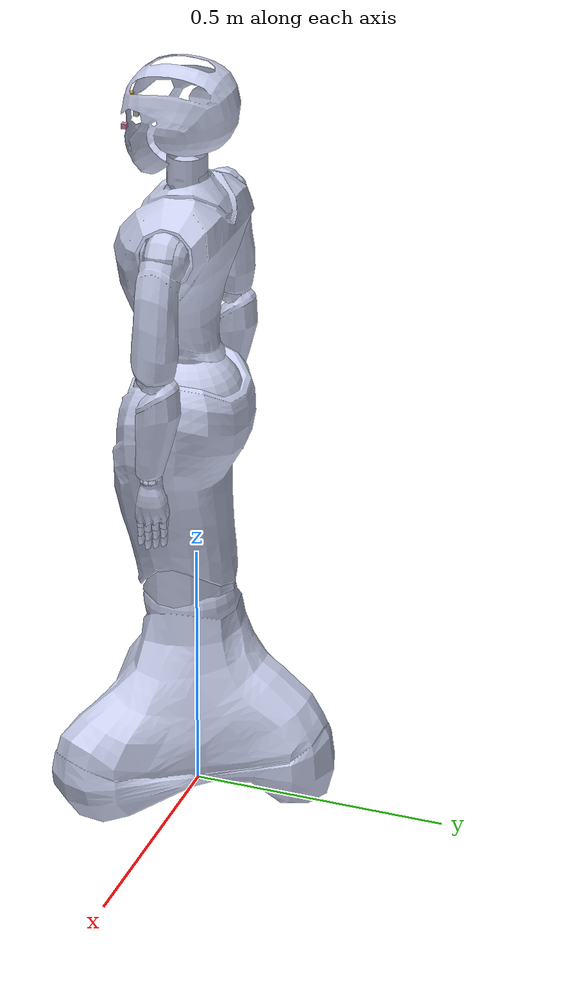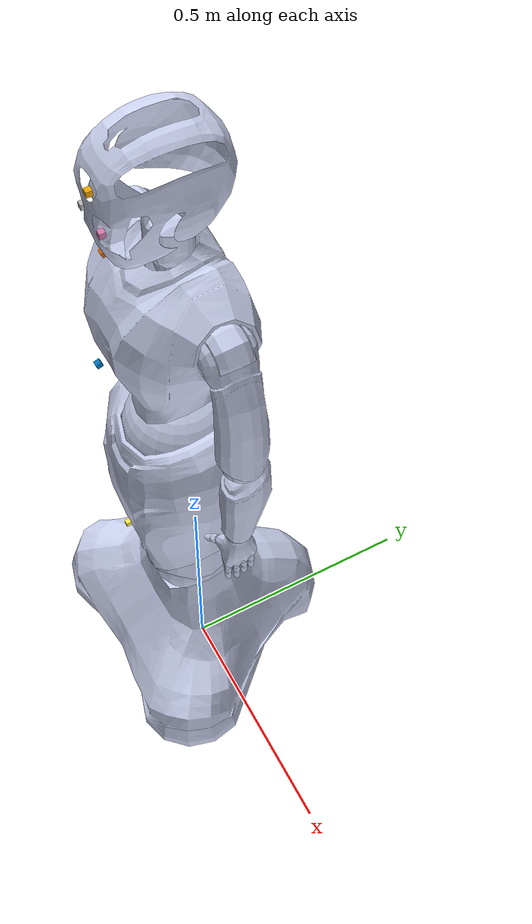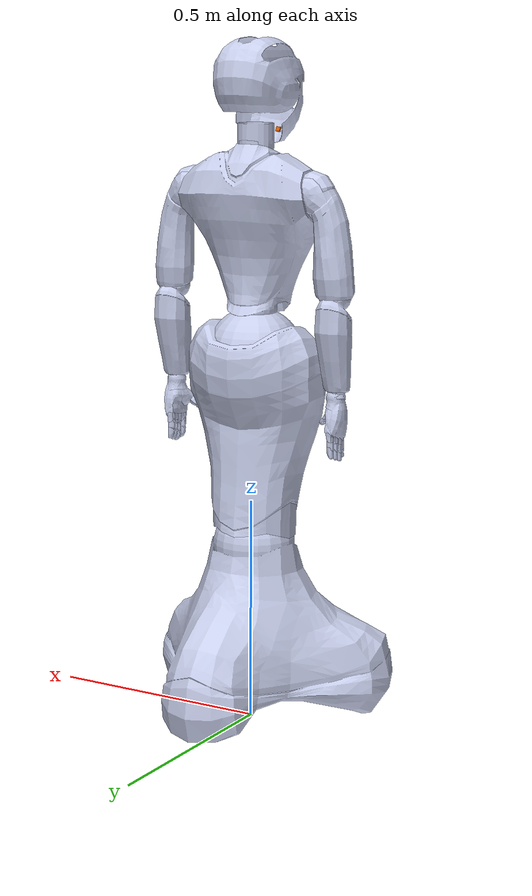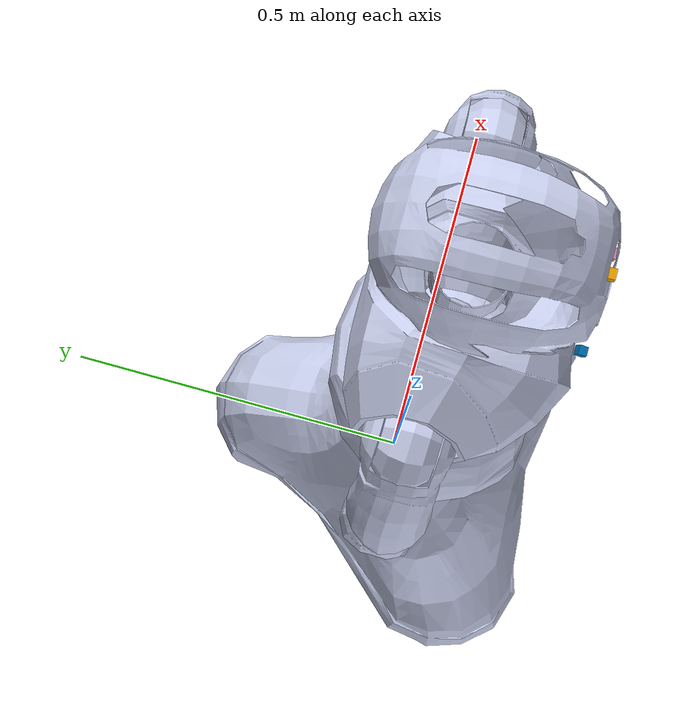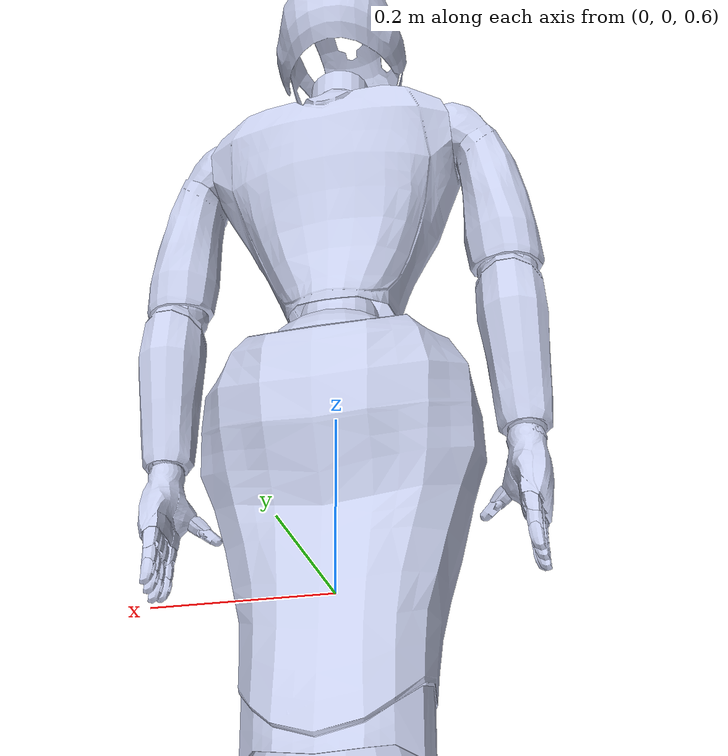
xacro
<?xml version="1.0"?>
<robot
  name="xr1" xmlns:xacro="http://www.ros.org/wiki/xacro">
  <!-- Import all Gazebo-customization elements, including Gazebo colors -->
  <xacro:include filename="$(find xr1urdf)/urdf/xr1.gazebo" />
  <xacro:property name="M_PI" value="3.1415926535897931" />
  <link
    name="base_link">
    <inertial>
      <origin
        xyz="3.7967E-06 -0.014178 0.36294"
        rpy="0 0 0" />
      <mass
        value="36.19" />
      <inertia
        ixx="0.2837"
        ixy="6.6528E-07"
        ixz="1.7113E-06"
        iyy="0.2837"
        iyz="-9.4304E-05"
        izz="0.4608" />
    </inertial>
    <visual>
      <origin
        xyz="0 0 0"
        rpy="0 0 0" />
      <geometry>
        <mesh
          filename="package://xr1urdf/meshes/base_link.STL" />
      </geometry>
      <material
        name="">
        <color
          rgba="0.79216 0.81961 0.93333 1" />
      </material>
    </visual>
    <collision>
      <origin
        xyz="0 0 0"
        rpy="0 0 0" />
      <geometry>
        <mesh
          filename="package://xr1urdf/meshes/base_link.STL" />
      </geometry>
    </collision>
  </link>
  <link
    name="Knee_Link">
    <inertial>
      <origin
        xyz="-0.0018369 -0.052916 -5.4938E-05"
        rpy="0 0 0" />
      <mass
        value="8.175" />
      <inertia
        ixx="0.09013"
        ixy="7.826E-06"
        ixz="-7.279E-06"
        iyy="0.1181"
        iyz="6.324E-05"
        izz="0.118" />
    </inertial>
    <visual>
      <origin
        xyz="0 0 0"
        rpy="0 0 0" />
      <geometry>
        <mesh
          filename="package://xr1urdf/meshes/Knee_Link.STL" />
      </geometry>
      <material
        name="">
        <color
          rgba="0.79216 0.81961 0.93333 1" />
      </material>
    </visual>
    <collision>
      <origin
        xyz="0 0 0"
        rpy="0 0 0" />
      <geometry>
        <mesh
          filename="package://xr1urdf/meshes/Knee_Link.STL" />
      </geometry>
    </collision>
  </link>
  <joint
    name="Knee_X"
    type="revolute">
    <origin
      xyz="5.4938E-05 -0.013143 0.40405"
      rpy="-1.5708 0.033734 -1.5708" />
    <parent
      link="base_link" />
    <child
      link="Knee_Link" />
    <axis
      xyz="0 0 1" />
    <limit
      lower = "-0.691"
      upper = "0.691"
      effort = "30"
      velocity = "3.14"/>
    <dynamics
      friction="0.1" />
  </joint>
  <link
    name="Leg_Link">
    <inertial>
      <origin
        xyz="0.0043847 -0.29449 -8.7888E-05"
        rpy="0 0 0" />
      <mass
        value="0.32293" />
      <inertia
        ixx="0.00058566"
        ixy="-2.0496E-05"
        ixz="3.9125E-09"
        iyy="7.173E-07"
        iyz="1.118E-07"
        izz="0.00058637" />
    </inertial>
    <visual>
      <origin
        xyz="0 0 0"
        rpy="0 0 0" />
      <geometry>
        <mesh
          filename="package://xr1urdf/meshes/Leg_Link.STL" />
      </geometry>
      <material
        name="">
        <color
          rgba="0.79216 0.81961 0.93333 1" />
      </material>
    </visual>
    <collision>
      <origin
        xyz="0 0 0"
        rpy="0 0 0" />
      <geometry>
        <mesh
          filename="package://xr1urdf/meshes/Leg_Link.STL" />
      </geometry>
    </collision>
  </link>
  <joint
    name="Leg_D"
    type="fixed">
    <origin
      xyz="0 0 0"
      rpy="0 0 6.9389E-18" />
    <parent
      link="Knee_Link" />
    <child
      link="Leg_Link" />
    <axis
      xyz="0 0 0" />
    <dynamics
      friction="0.1" />
  </joint>
  <link
    name="Thigh_Link">
    <inertial>
      <origin
        xyz="-0.013604 -0.00011257 0.42407"
        rpy="0 0 0" />
      <mass
        value="0.8847" />
      <inertia
        ixx="0.1604"
        ixy="0"
        ixz="0"
        iyy="0.1604"
        iyz="0"
        izz="0.1024" />
    </inertial>
    <visual>
      <origin
        xyz="0 0 0"
        rpy="0 0 0" />
      <geometry>
        <mesh
          filename="package://xr1urdf/meshes/Thigh_Link.STL" />
      </geometry>
      <material
        name="">
        <color
          rgba="0.79216 0.81961 0.93333 1" />
      </material>
    </visual>
    <collision>
      <origin
        xyz="0 0 0"
        rpy="0 0 0" />
      <geometry>
        <mesh
          filename="package://xr1urdf/meshes/Thigh_Link.STL" />
      </geometry>
    </collision>
  </link>
  <joint
    name="Back_Z"
    type="revolute">
    <origin
      xyz="0 0 0"
      rpy="1.5707 0 -0.0012161" />
    <parent
      link="Leg_Link" />
    <child
      link="Thigh_Link" />
    <axis
      xyz="-0.032512 -0.00013583 0.99947" />
    <limit
      lower = "-1.57"
      upper = "1.57"
      effort = "30"
      velocity = "3.14"/>
    <dynamics
      friction="0.1" />
  </joint>
  <link
    name="Thigh_Link2">
    <inertial>
      <origin
        xyz="1.3517E-08 -1.7091E-08 -5.4937E-05"
        rpy="0 0 0" />
      <mass
        value="0.6035" />
      <inertia
        ixx="0.1537"
        ixy="0"
        ixz="0"
        iyy="0.1537"
        iyz="0"
        izz="0.0968" />
    </inertial>
    <visual>
      <origin
        xyz="0 0 0"
        rpy="0 0 0" />
      <geometry>
        <mesh
          filename="package://xr1urdf/meshes/Thigh_Link2.STL" />
      </geometry>
      <material
        name="">
        <color
          rgba="0.79216 0.81961 0.93333 1" />
      </material>
    </visual>
    <collision>
      <origin
        xyz="0 0 0"
        rpy="0 0 0" />
      <geometry>
        <mesh
          filename="package://xr1urdf/meshes/Thigh_Link2.STL" />
      </geometry>
    </collision>
  </link>
  <joint
    name="Back_X"
    type="revolute">
    <origin
      xyz="-0.013604 -5.763E-05 0.42407"
      rpy="-1.5707 -0.032068 -4.3595E-06" />
    <parent
      link="Thigh_Link" />
    <child
      link="Thigh_Link2" />
    <axis
      xyz="0 0 1" />
    <limit
      lower = "-0.691"
      upper = "0.691"
      effort = "30"
      velocity = "3.14"/>
    <dynamics
      friction="0.1" />
  </joint>
  <link
    name="Back_Link">
    <inertial>
      <origin
        xyz="0.064471 3.1609E-05 0.017862"
        rpy="0 0 0" />
      <mass
        value="13.87" />
      <inertia
        ixx="0.09994"
        ixy="8.3465E-08"
        ixz="-0.00048977"
        iyy="0.1191"
        iyz="1.3363E-07"
        izz="0.1071" />
    </inertial>
    <visual>
      <origin
        xyz="0 0 0"
        rpy="0 0 0" />
      <geometry>
        <mesh
          filename="package://xr1urdf/meshes/Back_Link.STL" />
      </geometry>
      <material
        name="">
        <color
          rgba="0.79216 0.81961 0.93333 1" />
      </material>
    </visual>
    <collision>
      <origin
        xyz="0 0 0"
        rpy="0 0 0" />
      <geometry>
        <mesh
          filename="package://xr1urdf/meshes/Back_Link.STL" />
      </geometry>
    </collision>
  </link>
  <joint
    name="Back_Y"
    type="revolute">
    <origin
      xyz="-0.013865 -0.10565 -2.6926E-05"
      rpy="-1.5708 0 -1.5712" />
    <parent
      link="Thigh_Link2" />
    <child
      link="Back_Link" />
    <axis
      xyz="0 0 1" />
    <limit
      lower = "-1.01"
      upper = "1.01"
      effort = "30"
      velocity = "3.14"/>
    <dynamics
      friction="0.1" />
  </joint>
  <link
    name="Neck_Link">
    <inertial>
      <origin
        xyz="-0.00011159 0.026435 0.35317"
        rpy="0 0 0" />
      <mass
        value="0.6805" />
      <inertia
        ixx="0.0009499"
        ixy="0"
        ixz="0"
        iyy="0.0009499"
        iyz="0"
        izz="0.000722" />
    </inertial>
    <visual>
      <origin
        xyz="0 0 0"
        rpy="0 0 0" />
      <geometry>
        <mesh
          filename="package://xr1urdf/meshes/Neck_Link.STL" />
      </geometry>
      <material
        name="">
        <color
          rgba="0.79216 0.81961 0.93333 1" />
      </material>
    </visual>
    <collision>
      <origin
        xyz="0 0 0"
        rpy="0 0 0" />
      <geometry>
        <mesh
          filename="package://xr1urdf/meshes/Neck_Link.STL" />
      </geometry>
    </collision>
  </link>
  <joint
    name="Neck_Z"
    type="revolute">
    <origin
      xyz="0 0 0"
      rpy="-1.45576756643559 0.00585422888906165 -1.5707963267949" />
    <parent
      link="Back_Link" />
    <child
      link="Neck_Link" />
    <axis
      xyz="-6.48829923723553E-05 0.103758479857577 0.994602520431073" />
    <limit
      lower = "-1.57"
      upper = "1.57"
      effort = "30"
      velocity = "3.14"/>
  </joint>
  <link
    name="Neck_Link2">
    <inertial>
      <origin
        xyz="-0.00017003 -0.015117 -5.4883E-05"
        rpy="0 0 0" />
      <mass
        value="0.4417" />
      <inertia
        ixx="0.0003943"
        ixy="0"
        ixz="0"
        iyy="0.0003943"
        iyz="0"
        izz="0.000338" />
    </inertial>
    <visual>
      <origin
        xyz="0 0 0"
        rpy="0 0 0" />
      <geometry>
        <mesh
          filename="package://xr1urdf/meshes/Neck_Link2.STL" />
      </geometry>
      <material
        name="">
        <color
          rgba="0.79216 0.81961 0.93333 1" />
      </material>
    </visual>
    <collision>
      <origin
        xyz="0 0 0"
        rpy="0 0 0" />
      <geometry>
        <mesh
          filename="package://xr1urdf/meshes/Neck_Link2.STL" />
      </geometry>
    </collision>
  </link>
  <joint
    name="Neck_X"
    type="revolute">
    <origin
      xyz="-5.66462826414854E-05 0.0264756614309742 0.353526594203303"
      rpy="-1.570120763762 -0.103943394823006 -1.57668196274022" />
    <parent
      link="Neck_Link" />
    <child
      link="Neck_Link2" />
    <axis
      xyz="0 0 1" />
    <limit
      lower = "-1.01"
      upper = "0.628"
      effort = "30"
      velocity = "3.14"/>
  </joint>
  <link
    name="Head_Link">
    <inertial>
      <origin
        xyz="0.078614 2.5049E-06 0.024556"
        rpy="0 0 0" />
      <mass
        value="1.661" />
      <inertia
        ixx="0.01505"
        ixy="0"
        ixz="0"
        iyy="0.01505"
        iyz="0"
        izz="0.01212" />
    </inertial>
    <visual>
      <origin
        xyz="0 0 0"
        rpy="0 0 0" />
      <geometry>
        <mesh
          filename="package://xr1urdf/meshes/Head_Link.STL" />
      </geometry>
      <material
        name="">
        <color
          rgba="0.79216 0.81961 0.93333 1" />
      </material>
    </visual>
    <collision>
      <origin
        xyz="0 0 0"
        rpy="0 0 0" />
      <geometry>
        <mesh
          filename="package://xr1urdf/meshes/Head_Link.STL" />
      </geometry>
    </collision>
  </link>
  <joint
    name="Head_Y"
    type="revolute">
    <origin
      xyz="-0.0148356484587829 -0.0504585752470172 0"
      rpy="-1.5707963267949 0 -1.58187971499664" />
    <parent
      link="Neck_Link2" />
    <child
      link="Head_Link" />
    <axis
      xyz="0 0 1" />
    <limit
      lower = "-1.26"
      upper = "1.26"
      effort = "30"
      velocity = "3.14" />
  </joint>
  <link
    name="Left_Shoulder_Link">
    <inertial>
      <origin
        xyz="-4.1264E-05 -0.00075572 -0.00067551"
        rpy="0 0 0" />
      <mass
        value="0.8107" />
      <inertia
        ixx="0.08447"
        ixy="0"
        ixz="0"
        iyy="0.08447"
        iyz="0"
        izz="0.06554" />
    </inertial>
    <visual>
      <origin
        xyz="0 0 0"
        rpy="0 0 0" />
      <geometry>
        <mesh
          filename="package://xr1urdf/meshes/Left_Shoulder_Link.STL" />
      </geometry>
      <material
        name="">
        <color
          rgba="0.79216 0.81961 0.93333 1" />
      </material>
    </visual>
    <collision>
      <origin
        xyz="0 0 0"
        rpy="0 0 0" />
      <geometry>
        <mesh
          filename="package://xr1urdf/meshes/Left_Shoulder_Link.STL" />
      </geometry>
    </collision>
  </link>
  <joint
    name="Left_Shoulder_X"
    type="revolute">
    <origin
      xyz="0.25847 -0.15106 0.001585"
      rpy="1.9199 -1.5708 0" />
    <parent
      link="Back_Link" />
    <child
      link="Left_Shoulder_Link" />
    <axis
      xyz="0 0 1" />
    <limit
      lower = "-2.26"
      upper = "2.26"
      effort = "30"
      velocity = "3.14"/>
    <dynamics
      friction="0.1" />
  </joint>
  <link
    name="Left_Arm_Link">
    <inertial>
      <origin
        xyz="0.10178 0.03894 0.00067822"
        rpy="0 0 0" />
      <mass
        value="1.022" />
      <inertia
        ixx="0.05869"
        ixy="-5.2828E-05"
        ixz="-4.5659E-06"
        iyy="0.05866"
        iyz="-9.0249E-07"
        izz="0.01331" />
    </inertial>
    <visual>
      <origin
        xyz="0 0 0"
        rpy="0 0 0" />
      <geometry>
        <mesh
          filename="package://xr1urdf/meshes/Left_Arm_Link.STL" />
      </geometry>
      <material
        name="">
        <color
          rgba="0.79216 0.81961 0.93333 1" />
      </material>
    </visual>
    <collision>
      <origin
        xyz="0 0 0"
        rpy="0 0 0" />
      <geometry>
        <mesh
          filename="package://xr1urdf/meshes/Left_Arm_Link.STL" />
      </geometry>
    </collision>
  </link>
  <joint
    name="Left_Shoulder_Y"
    type="revolute">
    <origin
      xyz="0 0 0"
      rpy="1.5708 0.3491 1.5708" />
    <parent
      link="Left_Shoulder_Link" />
    <child
      link="Left_Arm_Link" />
    <axis
      xyz="0 0 1" />
    <limit
      lower = "-0.188"
      upper = "1.88"
      effort = "30"
      velocity = "3.14"/>
    <dynamics
      friction="0.1" />
  </joint>
  <link
    name="Left_Elbow_Link">
    <inertial>
      <origin
        xyz="7.2184E-05 5.6121E-05 -0.21867"
        rpy="0 0 0" />
      <mass
        value="0.7854" />
      <inertia
        ixx="0.02333"
        ixy="0"
        ixz="0"
        iyy="0.02333"
        iyz="0"
        izz="0.02" />
    </inertial>
    <visual>
      <origin
        xyz="0 0 0"
        rpy="0 0 0" />
      <geometry>
        <mesh
          filename="package://xr1urdf/meshes/Left_Elbow_Link.STL" />
      </geometry>
      <material
        name="">
        <color
          rgba="0.79216 0.81961 0.93333 1" />
      </material>
    </visual>
    <collision>
      <origin
        xyz="0 0 0"
        rpy="0 0 0" />
      <geometry>
        <mesh
          filename="package://xr1urdf/meshes/Left_Elbow_Link.STL" />
      </geometry>
    </collision>
  </link>
  <joint
    name="Left_Elbow_Z"
    type="revolute">
    <origin
      xyz="0 0.051343 0.0030704"
      rpy="-1.5708 0 1.5708" />
    <parent
      link="Left_Arm_Link" />
    <child
      link="Left_Elbow_Link" />
    <axis
      xyz="0 0 -1" />
    <limit
      lower = "-3.14"
      upper = "3.14"
      effort = "30"
      velocity = "3.14"/>
  </joint>
  <link
    name="Left_Forearm_Link">
    <inertial>
      <origin
        xyz="-0.004929 0.04719 0.00056402"
        rpy="0 0 0" />
      <mass
        value="0.6233" />
      <inertia
        ixx="0.01023"
        ixy="-3.6841E-06"
        ixz="3.8131E-08"
        iyy="0.01019"
        iyz="-5.0227E-07"
        izz="0.002818" />
    </inertial>
    <visual>
      <origin
        xyz="0 0 0"
        rpy="0 0 0" />
      <geometry>
        <mesh
          filename="package://xr1urdf/meshes/Left_Forearm_Link.STL" />
      </geometry>
      <material
        name="">
        <color
          rgba="0.79216 0.81961 0.93333 1" />
      </material>
    </visual>
    <collision>
      <origin
        xyz="0 0 0"
        rpy="0 0 0" />
      <geometry>
        <mesh
          filename="package://xr1urdf/meshes/Left_Forearm_Link.STL" />
      </geometry>
    </collision>
  </link>
  <joint
    name="Left_Elbow_X"
    type="revolute">
    <origin
      xyz="7.21835432308526E-05 5.61241489814741E-05 -0.218666930883292"
      rpy="-1.5707963267949 0 -1.5707963267949" />
    <parent
      link="Left_Elbow_Link" />
    <child
      link="Left_Forearm_Link" />
    <axis
      xyz="0 0 1" />
    <limit
      lower = "-1.57"
      upper = "0.1"
      effort = "30"
      velocity = "3.14"/>
  </joint>
  <link
    name="Left_Wrist_Link">
    <inertial>
      <origin
        xyz="0.0089917 -0.0016706 0.19203"
        rpy="0 0 0" />
      <mass
        value="0.5487" />
      <inertia
        ixx="0.01411"
        ixy="0"
        ixz="0"
        iyy="0.01411"
        iyz="0"
        izz="0.02687" />
    </inertial>
    <visual>
      <origin
        xyz="0 0 0"
        rpy="0 0 0" />
      <geometry>
        <mesh
          filename="package://xr1urdf/meshes/Left_Wrist_Link.STL" />
      </geometry>
      <material
        name="">
        <color
          rgba="0.79216 0.81961 0.93333 1" />
      </material>
    </visual>
    <collision>
      <origin
        xyz="0 0 0"
        rpy="0 0 0" />
      <geometry>
        <mesh
          filename="package://xr1urdf/meshes/Left_Wrist_Link.STL" />
      </geometry>
    </collision>
  </link>
  <joint
    name="Left_Wrist_Z"
    type="revolute">
    <origin
      xyz="0 0 0"
      rpy="-1.5707963267949 0 0" />
    <parent
      link="Left_Forearm_Link" />
    <child
      link="Left_Wrist_Link" />
    <axis
      xyz="0 0 1" />
    <limit
      lower = "-3.14"
      upper = "3.14"
      effort = "30"
      velocity = "3.14"/>
  </joint>
  <link
    name="Left_Wrist_Link2">
    <inertial>
      <origin
        xyz="0.012461 0.0028972 -0.08048"
        rpy="0 0 0" />
      <mass
        value="0.5362" />
      <inertia
        ixx="0.00512"
        ixy="0"
        ixz="0"
        iyy="0.00512"
        iyz="0"
        izz="0.00512" />
    </inertial>
    <visual>
      <origin
        xyz="-0.011375266 0 0.080476412"
        rpy="0 0 0" />
      <geometry>
        <mesh
          filename="package://xr1urdf/meshes/Left_Wrist_Link2.STL" />
      </geometry>
      <material
        name="">
        <color
          rgba="0.79216 0.81961 0.93333 1" />
      </material>
    </visual>
    <collision>
      <origin
        xyz="0 0 0"
        rpy="0 0 0" />
      <geometry>
        <mesh
          filename="package://xr1urdf/meshes/Left_Wrist_Link2.STL" />
      </geometry>
    </collision>
  </link>
  <joint
    name="Left_Wrist_Y"
    type="revolute">
    <origin
      xyz="0.00784287714185615 0.000519681604099265 0.219279727935792"
      rpy="-1.5707963267949 0 -1.5707963267949" />
    <parent
      link="Left_Wrist_Link" />
    <child
      link="Left_Wrist_Link2" />
    <axis
      xyz="0 0 1" />
    <limit
      lower = "-1.07"
      upper = "1.13"
      effort = "30"
      velocity = "3.14"/>
  </joint>
  <link
    name="Left_Hand_Link">
    <inertial>
      <origin
        xyz="0.031243 0.080045 0.012473"
        rpy="0 0 0" />
      <mass
        value="0.1449" />
      <inertia
        ixx="0.006855"
        ixy="0"
        ixz="0"
        iyy="0.005574"
        iyz="0"
        izz="0.00377" />
    </inertial>
    <visual>
      <origin
        xyz="0 -0.080476412 -0.011375266"
        rpy="0 0 0" />
      <geometry>
        <mesh
          filename="package://xr1urdf/meshes/Left_Hand_Link.STL" />
      </geometry>
      <material
        name="">
        <color
          rgba="0.79216 0.81961 0.93333 1" />
      </material>
    </visual>
    <collision>
      <origin
        xyz="0 0 0"
        rpy="0 0 0" />
      <geometry>
        <mesh
          filename="package://xr1urdf/meshes/Left_Hand_Link.STL" />
      </geometry>
    </collision>
  </link>
  <joint
    name="Left_Wrist_X"
    type="revolute">
    <origin
      xyz="0 0 0"
      rpy="-1.5707963267949 0 -1.5707963267949" />
    <parent
      link="Left_Wrist_Link2" />
    <child
      link="Left_Hand_Link" />
    <axis
      xyz="0 0 1" />
    <limit
      lower = "-0.88"
      upper = "0.754"
      effort = "30"
      velocity = "3.14"/>
  </joint>
  <link
    name="Left_1_1_Link">
    <inertial>
      <origin
        xyz="-0.002186 -0.0013399 -0.00013841"
        rpy="0 0 0" />
      <mass
        value="0.06844" />
      <inertia
        ixx="0.001031"
        ixy="-1.6265E-08"
        ixz="-1.6801E-09"
        iyy="0.001031"
        iyz="-1.0299E-09"
        izz="0.001501" />
    </inertial>
    <visual>
      <origin
        xyz="0 0 0"
        rpy="0 0 0" />
      <geometry>
        <mesh
          filename="package://xr1urdf/meshes/Left_1_1_Link.STL" />
      </geometry>
      <material
        name="">
        <color
          rgba="0.79216 0.81961 0.93333 1" />
      </material>
    </visual>
    <collision>
      <origin
        xyz="0 0 0"
        rpy="0 0 0" />
      <geometry>
        <mesh
          filename="package://xr1urdf/meshes/Left_1_1_Link.STL" />
      </geometry>
    </collision>
  </link>
  <joint
    name="Left_1_1_Joint"
    type="revolute">
    <origin
      xyz="0.0463873711048263 -0.0227514450525238 -0.0270481463075324"
      rpy="0 -1.00156316575 1.94835151482426" />
    <parent
      link="Left_Hand_Link" />
    <child
      link="Left_1_1_Link" />
    <axis
      xyz="0 0 1" />
    <limit
      lower = "0.0"
      upper = "1.21"
      effort = "30"
      velocity = "3.14"/>
  </joint>
  <link
    name="Left_1_2_Link">
    <inertial>
      <origin
        xyz="-0.0042083 -0.001782 -1.4605E-05"
        rpy="0 0 0" />
      <mass
        value="0.01812" />
      <inertia
        ixx="0.0005327"
        ixy="-1.8137E-08"
        ixz="-1.4873E-10"
        iyy="0.0007867"
        iyz="-6.2976E-11"
        izz="0.0005335" />
    </inertial>
    <visual>
      <origin
        xyz="0 0 0"
        rpy="0 0 0" />
      <geometry>
        <mesh
          filename="package://xr1urdf/meshes/Left_1_2_Link.STL" />
      </geometry>
      <material
        name="">
        <color
          rgba="0.79216 0.81961 0.93333 1" />
      </material>
    </visual>
    <collision>
      <origin
        xyz="0 0 0"
        rpy="0 0 0" />
      <geometry>
        <mesh
          filename="package://xr1urdf/meshes/Left_1_2_Link.STL" />
      </geometry>
    </collision>
  </link>
  <joint
    name="Left_1_2_Joint"
    type="revolute">
    <origin
      xyz="-0.0145863076944239 -0.00868903405537458 0"
      rpy="-6.90671092873486E-07 4.78610937881837E-07 -4.41951919144599E-07" />
    <parent
      link="Left_1_1_Link" />
    <child
      link="Left_1_2_Link" />
    <axis
      xyz="0 0 1" />
    <limit
      lower = "0.0"
      upper = "1.45"
      effort = "30"
      velocity = "3.14"/>
  </joint>
  <link
    name="Left_2_1_Link">
    <inertial>
      <origin
        xyz="6.0375E-05 -0.004442 -8.9343E-05"
        rpy="0 0 0" />
      <mass
        value="0.05105" />
      <inertia
        ixx="0.0017"
        ixy="1.0587E-09"
        ixz="2.1295E-11"
        iyy="0.0017"
        iyz="-1.5667E-09"
        izz="0.002498" />
    </inertial>
    <visual>
      <origin
        xyz="0 0 0"
        rpy="0 0 0" />
      <geometry>
        <mesh
          filename="package://xr1urdf/meshes/Left_2_1_Link.STL" />
      </geometry>
      <material
        name="">
        <color
          rgba="0.79216 0.81961 0.93333 1" />
      </material>
    </visual>
    <collision>
      <origin
        xyz="0 0 0"
        rpy="0 0 0" />
      <geometry>
        <mesh
          filename="package://xr1urdf/meshes/Left_2_1_Link.STL" />
      </geometry>
    </collision>
  </link>
  <joint
    name="Left_2_1_Joint"
    type="revolute">
    <origin
      xyz="0.07421799091684 -0.0211750333284337 -0.000927044928134585"
      rpy="1.5707963267949 -1.5707963267949 0" />
    <parent
      link="Left_Hand_Link" />
    <child
      link="Left_2_1_Link" />
    <axis
      xyz="0 0 -1" />
    <limit
      lower = "0.0"
      upper = "1.00"
      effort = "30"
      velocity = "3.14"/>
  </joint>
  <link
    name="Left_2_2_Link">
    <inertial>
      <origin
        xyz="0.0004717 -0.0059497 -0.00010746"
        rpy="0 0 0" />
      <mass
        value="0.01234" />
      <inertia
        ixx="0.0008295"
        ixy="5.6493E-09"
        ixz="1.0204E-10"
        iyy="0.0008295"
        iyz="-1.287E-09"
        izz="0.001208" />
    </inertial>
    <visual>
      <origin
        xyz="0 0 0"
        rpy="0 0 0" />
      <geometry>
        <mesh
          filename="package://xr1urdf/meshes/Left_2_2_Link.STL" />
      </geometry>
      <material
        name="">
        <color
          rgba="0.79216 0.81961 0.93333 1" />
      </material>
    </visual>
    <collision>
      <origin
        xyz="0 0 0"
        rpy="0 0 0" />
      <geometry>
        <mesh
          filename="package://xr1urdf/meshes/Left_2_2_Link.STL" />
      </geometry>
    </collision>
  </link>
  <joint
    name="Left_2_2_Joint"
    type="revolute">
    <origin
      xyz="0 -0.0180361175537143 0"
      rpy="0 0 0" />
    <parent
      link="Left_2_1_Link" />
    <child
      link="Left_2_2_Link" />
    <axis
      xyz="0 0 -1" />
    <limit
      lower = "0.0"
      upper = "1.20"
      effort = "30"
      velocity = "3.14"/>
  </joint>
  <link
    name="Left_2_3_Link">
    <inertial>
      <origin
        xyz="0.00082688 -0.0043373 -0.00010313"
        rpy="0 0 0" />
      <mass
        value="0.006588" />
      <inertia
        ixx="0.0002138"
        ixy="7.3617E-09"
        ixz="1.7504E-10"
        iyy="0.0003146"
        iyz="-9.1816E-10"
        izz="0.0002119" />
    </inertial>
    <visual>
      <origin
        xyz="0 0 0"
        rpy="0 0 0" />
      <geometry>
        <mesh
          filename="package://xr1urdf/meshes/Left_2_3_Link.STL" />
      </geometry>
      <material
        name="">
        <color
          rgba="0.79216 0.81961 0.93333 1" />
      </material>
    </visual>
    <collision>
      <origin
        xyz="0 0 0"
        rpy="0 0 0" />
      <geometry>
        <mesh
          filename="package://xr1urdf/meshes/Left_2_3_Link.STL" />
      </geometry>
    </collision>
  </link>
  <joint
    name="Left_2_3_Joint"
    type="revolute">
    <origin
      xyz="0 -0.0220256805419884 0"
      rpy="0 0 0" />
    <parent
      link="Left_2_2_Link" />
    <child
      link="Left_2_3_Link" />
    <axis
      xyz="0 0 -1" />
    <limit
      lower = "0.0"
      upper = "1.45"
      effort = "30"
      velocity = "3.14"/>
  </joint>
  <link
    name="Left_3_1_Link">
    <inertial>
      <origin
        xyz="0.00013722 -0.0054219 1.8135E-05"
        rpy="0 0 0" />
      <mass
        value="0.05197" />
      <inertia
        ixx="0.001723"
        ixy="3.2178E-09"
        ixz="-1.0762E-11"
        iyy="0.001723"
        iyz="4.2522E-10"
        izz="0.002543" />
    </inertial>
    <visual>
      <origin
        xyz="0 0 0"
        rpy="0 0 0" />
      <geometry>
        <mesh
          filename="package://xr1urdf/meshes/Left_3_1_Link.STL" />
      </geometry>
      <material
        name="">
        <color
          rgba="0.79216 0.81961 0.93333 1" />
      </material>
    </visual>
    <collision>
      <origin
        xyz="0 0 0"
        rpy="0 0 0" />
      <geometry>
        <mesh
          filename="package://xr1urdf/meshes/Left_3_1_Link.STL" />
      </geometry>
    </collision>
  </link>
  <joint
    name="Left_3_1_Joint"
    type="revolute">
    <origin
      xyz="0.0764901009021922 -0.00561489331473879 0.00175480169051168"
      rpy="1.5707963267949 -1.5707963267949 0" />
    <parent
      link="Left_Hand_Link" />
    <child
      link="Left_3_1_Link" />
    <axis
      xyz="0 0 -1" />
    <limit
      lower = "0.0"
      upper = "1.17"
      effort = "30"
      velocity = "3.14"/>
  </joint>
  <link
    name="Left_3_2_Link">
    <inertial>
      <origin
        xyz="0.00056785 -0.0061714 1.9798E-05"
        rpy="0 0 0" />
      <mass
        value="0.01299" />
      <inertia
        ixx="0.0008611"
        ixy="7.0543E-09"
        ixz="-2.2631E-11"
        iyy="0.0008611"
        iyz="2.4596E-10"
        izz="0.001271" />
    </inertial>
    <visual>
      <origin
        xyz="0 0 0"
        rpy="0 0 0" />
      <geometry>
        <mesh
          filename="package://xr1urdf/meshes/Left_3_2_Link.STL" />
      </geometry>
      <material
        name="">
        <color
          rgba="0.79216 0.81961 0.93333 1" />
      </material>
    </visual>
    <collision>
      <origin
        xyz="0 0 0"
        rpy="0 0 0" />
      <geometry>
        <mesh
          filename="package://xr1urdf/meshes/Left_3_2_Link.STL" />
      </geometry>
    </collision>
  </link>
  <joint
    name="Left_3_2_Joint"
    type="revolute">
    <origin
      xyz="0 -0.0205278778076161 0"
      rpy="0 0 0" />
    <parent
      link="Left_3_1_Link" />
    <child
      link="Left_3_2_Link" />
    <axis
      xyz="0 0 -1" />
    <limit
      lower = "0.0"
      upper = "1.41"
      effort = "30"
      velocity = "3.14"/>
  </joint>
  <link
    name="Left_3_3_Link">
    <inertial>
      <origin
        xyz="0.00092117 -0.0045548 2.1672E-05"
        rpy="0 0 0" />
      <mass
        value="0.006329" />
      <inertia
        ixx="0.0002073"
        ixy="8.6123E-09"
        ixz="-4.0979E-11"
        iyy="0.0003018"
        iyz="2.0262E-10"
        izz="0.0002056" />
    </inertial>
    <visual>
      <origin
        xyz="0 0 0"
        rpy="0 0 0" />
      <geometry>
        <mesh
          filename="package://xr1urdf/meshes/Left_3_3_Link.STL" />
      </geometry>
      <material
        name="">
        <color
          rgba="0.79216 0.81961 0.93333 1" />
      </material>
    </visual>
    <collision>
      <origin
        xyz="0 0 0"
        rpy="0 0 0" />
      <geometry>
        <mesh
          filename="package://xr1urdf/meshes/Left_3_3_Link.STL" />
      </geometry>
    </collision>
  </link>
  <joint
    name="Left_3_3_Joint"
    type="revolute">
    <origin
      xyz="0 -0.0220256042480496 0"
      rpy="0 0 0" />
    <parent
      link="Left_3_2_Link" />
    <child
      link="Left_3_3_Link" />
    <axis
      xyz="0 0 -1" />
    <limit
      lower = "0.0"
      upper = "1.69"
      effort = "30"
      velocity = "3.14"/>
  </joint>
  <link
    name="Left_4_1_Link">
    <inertial>
      <origin
        xyz="8.9301E-05 -0.0047682 6.5533E-05"
        rpy="0 0 0" />
      <mass
        value="0.04255" />
      <inertia
        ixx="0.001576"
        ixy="1.6758E-09"
        ixz="-2.3031E-11"
        iyy="0.001576"
        iyz="1.2297E-09"
        izz="0.002552" />
    </inertial>
    <visual>
      <origin
        xyz="0 0 0"
        rpy="0 0 0" />
      <geometry>
        <mesh
          filename="package://xr1urdf/meshes/Left_4_1_Link.STL" />
      </geometry>
      <material
        name="">
        <color
          rgba="0.79216 0.81961 0.93333 1" />
      </material>
    </visual>
    <collision>
      <origin
        xyz="0 0 0"
        rpy="0 0 0" />
      <geometry>
        <mesh
          filename="package://xr1urdf/meshes/Left_4_1_Link.STL" />
      </geometry>
    </collision>
  </link>
  <joint
    name="Left_4_1_Joint"
    type="revolute">
    <origin
      xyz="0.073528980296718 0.00968487170586999 0.000963213860921908"
      rpy="1.5707963267949 -1.5707963267949 0" />
    <parent
      link="Left_Hand_Link" />
    <child
      link="Left_4_1_Link" />
    <axis
      xyz="0 0 -1" />
    <limit
      lower = "0.0"
      upper = "1.20"
      effort = "30"
      velocity = "3.14"/>
  </joint>
  <link
    name="Left_4_2_Link">
    <inertial>
      <origin
        xyz="0.00050562 -0.0052511 7.4747E-05"
        rpy="0 0 0" />
      <mass
        value="0.01146" />
      <inertia
        ixx="0.0007867"
        ixy="5.3445E-09"
        ixz="-7.6075E-11"
        iyy="0.0007867"
        iyz="7.9006E-10"
        izz="0.001122" />
    </inertial>
    <visual>
      <origin
        xyz="0 0 0"
        rpy="0 0 0" />
      <geometry>
        <mesh
          filename="package://xr1urdf/meshes/Left_4_2_Link.STL" />
      </geometry>
      <material
        name="">
        <color
          rgba="0.79216 0.81961 0.93333 1" />
      </material>
    </visual>
    <collision>
      <origin
        xyz="0 0 0"
        rpy="0 0 0" />
      <geometry>
        <mesh
          filename="package://xr1urdf/meshes/Left_4_2_Link.STL" />
      </geometry>
    </collision>
  </link>
  <joint
    name="Left_4_2_Joint"
    type="revolute">
    <origin
      xyz="0 -0.0203540802001998 0"
      rpy="0 0 0" />
    <parent
      link="Left_4_1_Link" />
    <child
      link="Left_4_2_Link" />
    <axis
      xyz="0 0 -1" />
    <limit
      lower = "0.0"
      upper = "1.45"
      effort = "30"
      velocity = "3.14"/>
  </joint>
  <link
    name="Left_4_3_Link">
    <inertial>
      <origin
        xyz="0.00086014 -0.0036522 7.5558E-05"
        rpy="0 0 0" />
      <mass
        value="0.00662" />
      <inertia
        ixx="0.0002145"
        ixy="6.4482E-09"
        ixz="-1.334E-10"
        iyy="0.0003161"
        iyz="5.6641E-10"
        izz="0.0002127" />
    </inertial>
    <visual>
      <origin
        xyz="0 0 0"
        rpy="0 0 0" />
      <geometry>
        <mesh
          filename="package://xr1urdf/meshes/Left_4_3_Link.STL" />
      </geometry>
      <material
        name="">
        <color
          rgba="0.79216 0.81961 0.93333 1" />
      </material>
    </visual>
    <collision>
      <origin
        xyz="0 0 0"
        rpy="0 0 0" />
      <geometry>
        <mesh
          filename="package://xr1urdf/meshes/Left_4_3_Link.STL" />
      </geometry>
    </collision>
  </link>
  <joint
    name="Left_4_3_Joint"
    type="revolute">
    <origin
      xyz="0 -0.0220256805419927 0"
      rpy="0 0 0" />
    <parent
      link="Left_4_2_Link" />
    <child
      link="Left_4_3_Link" />
    <axis
      xyz="0 0 -1" />
    <limit
      lower = "0.0"
      upper = "1.74"
      effort = "30"
      velocity = "3.14"/>
  </joint>
  <link
    name="Left_5_1_Link">
    <inertial>
      <origin
        xyz="-0.00046586 -0.0042115 8.9979E-05"
        rpy="0 0 0" />
      <mass
        value="0.0465" />
      <inertia
        ixx="0.001585"
        ixy="-6.979E-09"
        ixz="1.4911E-10"
        iyy="0.001585"
        iyz="1.3479E-09"
        izz="0.002229" />
    </inertial>
    <visual>
      <origin
        xyz="0 0 0"
        rpy="0 0 0" />
      <geometry>
        <mesh
          filename="package://xr1urdf/meshes/Left_5_1_Link.STL" />
      </geometry>
      <material
        name="">
        <color
          rgba="0.79216 0.81961 0.93333 1" />
      </material>
    </visual>
    <collision>
      <origin
        xyz="0 0 0"
        rpy="0 0 0" />
      <geometry>
        <mesh
          filename="package://xr1urdf/meshes/Left_5_1_Link.STL" />
      </geometry>
    </collision>
  </link>
  <joint
    name="Left_5_1_Joint"
    type="revolute">
    <origin
      xyz="0.0702912178455524 0.0248770065332455 0.00038803380721289"
      rpy="1.5707963267949 -1.5707963267949 0" />
    <parent
      link="Left_Hand_Link" />
    <child
      link="Left_5_1_Link" />
    <axis
      xyz="0 0 -1" />
    <limit
      lower = "0.0"
      upper = "1.30"
      effort = "30"
      velocity = "3.14"/>
  </joint>
  <link
    name="Left_5_2_Link">
    <inertial>
      <origin
        xyz="-0.00012673 -0.0053846 9.956E-05"
        rpy="0 0 0" />
      <mass
        value="0.01531" />
      <inertia
        ixx="0.0006332"
        ixy="-1.3738E-09"
        ixz="2.5402E-11"
        iyy="0.0006332"
        iyz="1.0791E-09"
        izz="0.001025" />
    </inertial>
    <visual>
      <origin
        xyz="0 0 0"
        rpy="0 0 0" />
      <geometry>
        <mesh
          filename="package://xr1urdf/meshes/Left_5_2_Link.STL" />
      </geometry>
      <material
        name="">
        <color
          rgba="0.79216 0.81961 0.93333 1" />
      </material>
    </visual>
    <collision>
      <origin
        xyz="0 0 0"
        rpy="0 0 0" />
      <geometry>
        <mesh
          filename="package://xr1urdf/meshes/Left_5_2_Link.STL" />
      </geometry>
    </collision>
  </link>
  <joint
    name="Left_5_2_Joint"
    type="revolute">
    <origin
      xyz="0 -0.0182607269287086 0"
      rpy="0 0 0" />
    <parent
      link="Left_5_1_Link" />
    <child
      link="Left_5_2_Link" />
    <axis
      xyz="0 0 -1" />
    <limit
      lower = "0.0"
      upper = "1.56"
      effort = "30"
      velocity = "3.14"/>
  </joint>
  <link
    name="Left_5_3_Link">
    <inertial>
      <origin
        xyz="0.00024002 -0.0037831 9.9892E-05"
        rpy="0 0 0" />
      <mass
        value="0.007844" />
      <inertia
        ixx="0.0003171"
        ixy="1.8637E-09"
        ixz="-4.9209E-11"
        iyy="0.0005152"
        iyz="7.7571E-10"
        izz="0.0003161" />
    </inertial>
    <visual>
      <origin
        xyz="0 0 0"
        rpy="0 0 0" />
      <geometry>
        <mesh
          filename="package://xr1urdf/meshes/Left_5_3_Link.STL" />
      </geometry>
      <material
        name="">
        <color
          rgba="0.79216 0.81961 0.93333 1" />
      </material>
    </visual>
    <collision>
      <origin
        xyz="0 0 0"
        rpy="0 0 0" />
      <geometry>
        <mesh
          filename="package://xr1urdf/meshes/Left_5_3_Link.STL" />
      </geometry>
    </collision>
  </link>
  <joint
    name="Left_5_3_Joint"
    type="revolute">
    <origin
      xyz="0 -0.0220256805419934 0"
      rpy="0 0 0" />
    <parent
      link="Left_5_2_Link" />
    <child
      link="Left_5_3_Link" />
    <axis
      xyz="0 0 -1" />
    <limit
      lower = "0.0"
      upper = "1.87"
      effort = "30"
      velocity = "3.14"/>
  </joint>
  <link
    name="Right_Shoulder_Link">
    <inertial>
      <origin
        xyz="-4.1264E-05 -0.00075525 0.00067603"
        rpy="0 0 0" />
      <mass
        value="0.8107" />
      <inertia
        ixx="0.08441"
        ixy="0"
        ixz="0"
        iyy="0.08441"
        iyz="0"
        izz="0.06554" />
    </inertial>
    <visual>
      <origin
        xyz="0 0 0"
        rpy="0 0 0" />
      <geometry>
        <mesh
          filename="package://xr1urdf/meshes/Right_Shoulder_Link.STL" />
      </geometry>
      <material
        name="">
        <color
          rgba="0.79216 0.81961 0.93333 1" />
      </material>
    </visual>
    <collision>
      <origin
        xyz="0 0 0"
        rpy="0 0 0" />
      <geometry>
        <mesh
          filename="package://xr1urdf/meshes/Right_Shoulder_Link.STL" />
      </geometry>
    </collision>
  </link>
  <joint
    name="Right_Shoulder_X"
    type="revolute">
    <origin
      xyz="0.25847 0.15112 0.001585"
      rpy="1.2217 -1.5708 0" />
    <parent
      link="Back_Link" />
    <child
      link="Right_Shoulder_Link" />
    <axis
      xyz="0 0.00069016 1" />
    <dynamics
      friction="0.1" />
    <limit
      lower = "-2.26"
      upper = "2.26"
      effort = "30"
      velocity = "3.14"/>
  </joint>
  <link
    name="Right_Arm_Link">
    <inertial>
      <origin
        xyz="0.10162 -0.03901 0.0051548"
        rpy="0 0 0" />
      <mass
        value="1.022" />
      <inertia
        ixx="0.05869"
        ixy="5.2856E-05"
        ixz="-1.2809E-05"
        iyy="0.05866"
        iyz="3.2344E-06"
        izz="0.01331" />
    </inertial>
    <visual>
      <origin
        xyz="0 0 0"
        rpy="0 0 0" />
      <geometry>
        <mesh
          filename="package://xr1urdf/meshes/Right_Arm_Link.STL" />
      </geometry>
      <material
        name="">
        <color
          rgba="0.79216 0.81961 0.93333 1" />
      </material>
    </visual>
    <collision>
      <origin
        xyz="0 0 0"
        rpy="0 0 0" />
      <geometry>
        <mesh
          filename="package://xr1urdf/meshes/Right_Arm_Link.STL" />
      </geometry>
    </collision>
  </link>
  <joint
    name="Right_Shoulder_Y"
    type="revolute">
    <origin
      xyz="0 0 0"
      rpy="1.5708 -0.3491 1.6148" />
    <parent
      link="Right_Shoulder_Link" />
    <child
      link="Right_Arm_Link" />
    <axis
      xyz="-0.043991 3.039E-05 0.99903" />
    <dynamics
      friction="0.1" />
    <limit
      lower = "-1.88"
      upper = "0.188"
      effort = "30"
      velocity = "3.14"/>
  </joint>
  <link
    name="Right_Elbow_Link">
    <inertial>
      <origin
        xyz="0.00023182 -2.5152E-05 -0.21867"
        rpy="0 0 0" />
      <mass
        value="0.7854" />
      <inertia
        ixx="0.02333"
        ixy="0"
        ixz="0"
        iyy="0.02333"
        iyz="0"
        izz="0.02" />
    </inertial>
    <visual>
      <origin
        xyz="0 0 0"
        rpy="0 0 0" />
      <geometry>
        <mesh
          filename="package://xr1urdf/meshes/Right_Elbow_Link.STL" />
      </geometry>
      <material
        name="">
        <color
          rgba="0.79216 0.81961 0.93333 1" />
      </material>
    </visual>
    <collision>
      <origin
        xyz="0 0 0"
        rpy="0 0 0" />
      <geometry>
        <mesh
          filename="package://xr1urdf/meshes/Right_Elbow_Link.STL" />
      </geometry>
    </collision>
  </link>
  <joint
    name="Right_Elbow_Z"
    type="revolute">
    <origin
      xyz="-0.00016706 -0.051647 0.0029862"
      rpy="-1.6148 0 1.5701" />
    <parent
      link="Right_Arm_Link" />
    <child
      link="Right_Elbow_Link" />
    <axis
      xyz="0 0 -1" />
    <limit
      lower = "-3.14"
      upper = "3.14"
      effort = "30"
      velocity = "3.14"/>
  </joint>
  <link
    name="Right_Foream_Link">
    <inertial>
      <origin
        xyz="-0.0049256 0.047194 -0.00018363"
        rpy="0 0 0" />
      <mass
        value="0.6233" />
      <inertia
        ixx="0.01023"
        ixy="-3.6866E-06"
        ixz="-7.2573E-08"
        iyy="0.01019"
        iyz="-1.7964E-06"
        izz="0.002818" />
    </inertial>
    <visual>
      <origin
        xyz="0 0 0"
        rpy="0 0 0" />
      <geometry>
        <mesh
          filename="package://xr1urdf/meshes/Right_Foream_Link.STL" />
      </geometry>
      <material
        name="">
        <color
          rgba="0.79216 0.81961 0.93333 1" />
      </material>
    </visual>
    <collision>
      <origin
        xyz="0 0 0"
        rpy="0 0 0" />
      <geometry>
        <mesh
          filename="package://xr1urdf/meshes/Right_Foream_Link.STL" />
      </geometry>
    </collision>
  </link>
  <joint
    name="Right_Elbow_X"
    type="revolute">
    <origin
      xyz="0.00023182210159195 -2.51481413512666E-05 -0.218666825669526"
      rpy="-1.57947630138636 0 -1.5767307988545" />
    <parent
      link="Right_Elbow_Link" />
    <child
      link="Right_Foream_Link" />
    <axis
      xyz="-0.00593443722633651 -0.0086797127543666 0.99994472099277" />
    <limit
      lower = "-1.57"
      upper = "0.1"
      effort = "30"
      velocity = "3.14"/>
  </joint>
  <link
    name="Right_Wrist_Link">
    <inertial>
      <origin
        xyz="0.0090015 0.0016172 0.19203"
        rpy="0 0 0" />
      <mass
        value="0.5484" />
      <inertia
        ixx="0.01411"
        ixy="0"
        ixz="0"
        iyy="0.01411"
        iyz="0"
        izz="0.02685" />
    </inertial>
    <visual>
      <origin
        xyz="0 0 0"
        rpy="0 0 0" />
      <geometry>
        <mesh
          filename="package://xr1urdf/meshes/Right_Wrist_Link.STL" />
      </geometry>
      <material
        name="">
        <color
          rgba="0.79216 0.81961 0.93333 1" />
      </material>
    </visual>
    <collision>
      <origin
        xyz="0 0 0"
        rpy="0 0 0" />
      <geometry>
        <mesh
          filename="package://xr1urdf/meshes/Right_Wrist_Link.STL" />
      </geometry>
    </collision>
  </link>
  <joint
    name="Right_Wrist_Z"
    type="revolute">
    <origin
      xyz="0 0 0"
      rpy="-1.56211635220343 -8.67361737988404E-19 0" />
    <parent
      link="Right_Foream_Link" />
    <child
      link="Right_Wrist_Link" />
    <axis
      xyz="0 0 1" />
    <limit
      lower = "-3.14"
      upper = "3.14"
      effort = "30"
      velocity = "3.14"/>
  </joint>
  <link
    name="Right_Wrist_Link2">
    <inertial>
      <origin
        xyz="-1.7158E-08 -7.9833E-09 1.7109E-08"
        rpy="0 0 0" />
      <mass
        value="0.5362" />
      <inertia
        ixx="0.00512"
        ixy="0"
        ixz="0"
        iyy="0.00512"
        iyz="0"
        izz="0.00512" />
    </inertial>
    <visual>
      <origin
        xyz="0 0 0"
        rpy="0 0 0" />
      <geometry>
        <mesh
          filename="package://xr1urdf/meshes/Right_Wrist_Link2.STL" />
      </geometry>
      <material
        name="">
        <color
          rgba="0.79216 0.81961 0.93333 1" />
      </material>
    </visual>
    <collision>
      <origin
        xyz="0 0 0"
        rpy="0 0 0" />
      <geometry>
        <mesh
          filename="package://xr1urdf/meshes/Right_Wrist_Link2.STL" />
      </geometry>
    </collision>
  </link>
  <joint
    name="Right_Wrist_Y"
    type="revolute">
    <origin
      xyz="0.00784287714185615 0.000519681604099265 0.219279727935792"
      rpy="-1.5707963267949 0 -1.5767307988545" />
    <parent
      link="Right_Wrist_Link" />
    <child
      link="Right_Wrist_Link2" />
    <axis
      xyz="0 0 1" />
    <limit
      lower = "-1.13"
      upper = "1.07"
      effort = "30"
      velocity = "3.14"/>
  </joint>
  <link
    name="Right_Hand_Link">
    <inertial>
      <origin
        xyz="0.03414 -0.00043423 9.7572E-05"
        rpy="0 0 0" />
      <mass
        value="0.1449" />
      <inertia
        ixx="0.006892"
        ixy="0"
        ixz="0"
        iyy="0.005566"
        iyz="0"
        izz="0.003742" />
    </inertial>
    <visual>
      <origin
        xyz="0 0 0"
        rpy="0 0 0" />
      <geometry>
        <mesh
          filename="package://xr1urdf/meshes/Right_Hand_Link.STL" />
      </geometry>
      <material
        name="">
        <color
          rgba="0.79216 0.81961 0.93333 1" />
      </material>
    </visual>
    <collision>
      <origin
        xyz="0 0 0"
        rpy="0 0 0" />
      <geometry>
        <mesh
          filename="package://xr1urdf/meshes/Right_Hand_Link.STL" />
      </geometry>
    </collision>
  </link>
  <joint
    name="Right_Wrist_X"
    type="revolute">
    <origin
      xyz="0 0 0"
      rpy="-1.5707963267949 1.89103620342991E-16 -1.5707963267949" />
    <parent
      link="Right_Wrist_Link2" />
    <child
      link="Right_Hand_Link" />
    <axis
      xyz="0 0 1" />
    <limit
      lower = "-0.88"
      upper = "0.754"
      effort = "30"
      velocity = "3.14"/>
  </joint>
  <link
    name="Right_1_1_Link">
    <inertial>
      <origin
        xyz="0.0018576 -0.0017673 -0.00013841"
        rpy="0 0 0" />
      <mass
        value="0.0648" />
      <inertia
        ixx="0.001983"
        ixy="1.823E-08"
        ixz="1.4278E-09"
        iyy="0.001983"
        iyz="-1.3583E-09"
        izz="0.002841" />
    </inertial>
    <visual>
      <origin
        xyz="0 0 0"
        rpy="0 0 0" />
      <geometry>
        <mesh
          filename="package://xr1urdf/meshes/Right_1_1_Link.STL" />
      </geometry>
      <material
        name="">
        <color
          rgba="0.79216 0.81961 0.93333 1" />
      </material>
    </visual>
    <collision>
      <origin
        xyz="0 0 0"
        rpy="0 0 0" />
      <geometry>
        <mesh
          filename="package://xr1urdf/meshes/Right_1_1_Link.STL" />
      </geometry>
    </collision>
  </link>
  <joint
    name="Right_1_1_Joint"
    type="revolute">
    <origin
      xyz="0.0463873711048263 -0.0227514450525238 0.0270481463075324"
      rpy="-2.82585434013322 -0.967918454119807 -1.5707963267949" />
    <parent
      link="Right_Hand_Link" />
    <child
      link="Right_1_1_Link" />
    <axis
      xyz="0 0 -1" />
    <limit
      lower = "0.0"
      upper = "1.21"
      effort = "30"
      velocity = "3.14"/>
  </joint>
  <link
    name="Right_1_2_Link">
    <inertial>
      <origin
        xyz="0.0037429 -0.0026223 -1.4605E-05"
        rpy="0 0 0" />
      <mass
        value="0.01812" />
      <inertia
        ixx="0.0001332"
        ixy="2.3738E-08"
        ixz="1.3228E-10"
        iyy="0.0001972"
        iyz="-9.2673E-11"
        izz="0.0001339" />
    </inertial>
    <visual>
      <origin
        xyz="0 0 0"
        rpy="0 0 0" />
      <geometry>
        <mesh
          filename="package://xr1urdf/meshes/Right_1_2_Link.STL" />
      </geometry>
      <material
        name="">
        <color
          rgba="0.79216 0.81961 0.93333 1" />
      </material>
    </visual>
    <collision>
      <origin
        xyz="0 0 0"
        rpy="0 0 0" />
      <geometry>
        <mesh
          filename="package://xr1urdf/meshes/Right_1_2_Link.STL" />
      </geometry>
    </collision>
  </link>
  <joint
    name="Right_1_2_Joint"
    type="revolute">
    <origin
      xyz="0.0124478206926872 -0.0115460575511548 0"
      rpy="-7.75457443313983E-07 -3.23667641410902E-07 1.05731325888986E-07" />
    <parent
      link="Right_1_1_Link" />
    <child
      link="Right_1_2_Link" />
    <axis
      xyz="0 0 -1" />
    <limit
      lower = "0.0"
      upper = "1.45"
      effort = "30"
      velocity = "3.14"/>
  </joint>
  <link
    name="Right_2_1_Link">
    <inertial>
      <origin
        xyz="-6.0375E-05 -0.004442 -8.9343E-05"
        rpy="0 0 0" />
      <mass
        value="0.05105" />
      <inertia
        ixx="0.0017"
        ixy="-1.0587E-09"
        ixz="-2.1295E-11"
        iyy="0.0017"
        iyz="-1.5667E-09"
        izz="0.002498" />
    </inertial>
    <visual>
      <origin
        xyz="0 0 0"
        rpy="0 0 0" />
      <geometry>
        <mesh
          filename="package://xr1urdf/meshes/Right_2_1_Link.STL" />
      </geometry>
      <material
        name="">
        <color
          rgba="0.79216 0.81961 0.93333 1" />
      </material>
    </visual>
    <collision>
      <origin
        xyz="0 0 0"
        rpy="0 0 0" />
      <geometry>
        <mesh
          filename="package://xr1urdf/meshes/Right_2_1_Link.STL" />
      </geometry>
    </collision>
  </link>
  <joint
    name="Right_2_1_Joint"
    type="revolute">
    <origin
      xyz="0.07421799091684 -0.0211750333284337 0.000927044928134585"
      rpy="1.5707963267949 -1.5707963267949 0" />
    <parent
      link="Right_Hand_Link" />
    <child
      link="Right_2_1_Link" />
    <axis
      xyz="0 0 1" />
    <limit
      lower = "0.0"
      upper = "1.00"
      effort = "30"
      velocity = "3.14"/>
  </joint>
  <link
    name="Right_2_2_Link">
    <inertial>
      <origin
        xyz="-0.0004717 -0.0059497 -0.00010746"
        rpy="0 0 0" />
      <mass
        value="0.01234" />
      <inertia
        ixx="0.0008295"
        ixy="-5.6493E-09"
        ixz="-1.0204E-10"
        iyy="0.0008295"
        iyz="-1.287E-09"
        izz="0.001208" />
    </inertial>
    <visual>
      <origin
        xyz="0 0 0"
        rpy="0 0 0" />
      <geometry>
        <mesh
          filename="package://xr1urdf/meshes/Right_2_2_Link.STL" />
      </geometry>
      <material
        name="">
        <color
          rgba="0.79216 0.81961 0.93333 1" />
      </material>
    </visual>
    <collision>
      <origin
        xyz="0 0 0"
        rpy="0 0 0" />
      <geometry>
        <mesh
          filename="package://xr1urdf/meshes/Right_2_2_Link.STL" />
      </geometry>
    </collision>
  </link>
  <joint
    name="Right_2_2_Joint"
    type="revolute">
    <origin
      xyz="0 -0.0180361175537143 0"
      rpy="0 0 0" />
    <parent
      link="Right_2_1_Link" />
    <child
      link="Right_2_2_Link" />
    <axis
      xyz="0 0 1" />
    <limit
      lower = "0.0"
      upper = "1.20"
      effort = "30"
      velocity = "3.14"/>
  </joint>
  <link
    name="Right_2_3_Link">
    <inertial>
      <origin
        xyz="-0.00082688 -0.0043373 -0.00010313"
        rpy="0 0 0" />
      <mass
        value="0.006588" />
      <inertia
        ixx="0.0004257"
        ixy="-7.3617E-09"
        ixz="-1.7504E-10"
        iyy="0.0006273"
        iyz="-9.1816E-10"
        izz="0.0004238" />
    </inertial>
    <visual>
      <origin
        xyz="0 0 0"
        rpy="0 0 0" />
      <geometry>
        <mesh
          filename="package://xr1urdf/meshes/Right_2_3_Link.STL" />
      </geometry>
      <material
        name="">
        <color
          rgba="0.79216 0.81961 0.93333 1" />
      </material>
    </visual>
    <collision>
      <origin
        xyz="0 0 0"
        rpy="0 0 0" />
      <geometry>
        <mesh
          filename="package://xr1urdf/meshes/Right_2_3_Link.STL" />
      </geometry>
    </collision>
  </link>
  <joint
    name="Right_2_3_Joint"
    type="revolute">
    <origin
      xyz="0 -0.0220256805419884 0"
      rpy="0 0 0" />
    <parent
      link="Right_2_2_Link" />
    <child
      link="Right_2_3_Link" />
    <axis
      xyz="0 0 1" />
    <limit
      lower = "0.0"
      upper = "1.45"
      effort = "30"
      velocity = "3.14"/>
  </joint>
  <link
    name="Right_3_1_Link">
    <inertial>
      <origin
        xyz="-0.00013722 -0.0054219 1.8135E-05"
        rpy="0 0 0" />
      <mass
        value="0.05197" />
      <inertia
        ixx="0.001723"
        ixy="-3.2178E-09"
        ixz="1.0762E-11"
        iyy="0.001723"
        iyz="4.2522E-10"
        izz="0.002543" />
    </inertial>
    <visual>
      <origin
        xyz="0 0 0"
        rpy="0 0 0" />
      <geometry>
        <mesh
          filename="package://xr1urdf/meshes/Right_3_1_Link.STL" />
      </geometry>
      <material
        name="">
        <color
          rgba="0.79216 0.81961 0.93333 1" />
      </material>
    </visual>
    <collision>
      <origin
        xyz="0 0 0"
        rpy="0 0 0" />
      <geometry>
        <mesh
          filename="package://xr1urdf/meshes/Right_3_1_Link.STL" />
      </geometry>
    </collision>
  </link>
  <joint
    name="Right_3_1_Joint"
    type="revolute">
    <origin
      xyz="0.0764901009021922 -0.00561489331473879 -0.00175480169051168"
      rpy="1.5707963267949 -1.5707963267949 0" />
    <parent
      link="Right_Hand_Link" />
    <child
      link="Right_3_1_Link" />
    <axis
      xyz="0 0 1" />
    <limit
      lower = "0.0"
      upper = "1.17"
      effort = "30"
      velocity = "3.14"/>
  </joint>
  <link
    name="Right_3_2_Link">
    <inertial>
      <origin
        xyz="-0.00056785 -0.0061714 1.9798E-05"
        rpy="0 0 0" />
      <mass
        value="0.01299" />
      <inertia
        ixx="0.0008611"
        ixy="-7.0543E-09"
        ixz="2.2631E-11"
        iyy="0.0008611"
        iyz="2.4596E-10"
        izz="0.001271" />
    </inertial>
    <visual>
      <origin
        xyz="0 0 0"
        rpy="0 0 0" />
      <geometry>
        <mesh
          filename="package://xr1urdf/meshes/Right_3_2_Link.STL" />
      </geometry>
      <material
        name="">
        <color
          rgba="0.79216 0.81961 0.93333 1" />
      </material>
    </visual>
    <collision>
      <origin
        xyz="0 0 0"
        rpy="0 0 0" />
      <geometry>
        <mesh
          filename="package://xr1urdf/meshes/Right_3_2_Link.STL" />
      </geometry>
    </collision>
  </link>
  <joint
    name="Right_3_2_Joint"
    type="revolute">
    <origin
      xyz="0 -0.0205278778076158 0"
      rpy="0 0 0" />
    <parent
      link="Right_3_1_Link" />
    <child
      link="Right_3_2_Link" />
    <axis
      xyz="0 0 1" />
    <limit
      lower = "0.0"
      upper = "1.41"
      effort = "30"
      velocity = "3.14"/>
  </joint>
  <link
    name="Right_3_3_Link">
    <inertial>
      <origin
        xyz="-0.00092117 -0.0045548 2.1672E-05"
        rpy="0 0 0" />
      <mass
        value="0.006329" />
      <inertia
        ixx="0.0004128"
        ixy="-8.6123E-09"
        ixz="4.0979E-11"
        iyy="0.0006019"
        iyz="2.0262E-10"
        izz="0.0004111" />
    </inertial>
    <visual>
      <origin
        xyz="0 0 0"
        rpy="0 0 0" />
      <geometry>
        <mesh
          filename="package://xr1urdf/meshes/Right_3_3_Link.STL" />
      </geometry>
      <material
        name="">
        <color
          rgba="0.79216 0.81961 0.93333 1" />
      </material>
    </visual>
    <collision>
      <origin
        xyz="0 0 0"
        rpy="0 0 0" />
      <geometry>
        <mesh
          filename="package://xr1urdf/meshes/Right_3_3_Link.STL" />
      </geometry>
    </collision>
  </link>
  <joint
    name="Right_3_3_Joint"
    type="revolute">
    <origin
      xyz="0 -0.0220256042480499 0"
      rpy="0 0 0" />
    <parent
      link="Right_3_2_Link" />
    <child
      link="Right_3_3_Link" />
    <axis
      xyz="0 0 1" />
    <limit
      lower = "0.0"
      upper = "1.69"
      effort = "30"
      velocity = "3.14"/>
  </joint>
  <link
    name="Right_4_1_Link">
    <inertial>
      <origin
        xyz="-8.9301E-05 -0.0047682 6.5533E-05"
        rpy="0 0 0" />
      <mass
        value="0.04255" />
      <inertia
        ixx="0.001576"
        ixy="-1.6758E-09"
        ixz="2.3031E-11"
        iyy="0.001576"
        iyz="1.2297E-09"
        izz="0.002552" />
    </inertial>
    <visual>
      <origin
        xyz="0 0 0"
        rpy="0 0 0" />
      <geometry>
        <mesh
          filename="package://xr1urdf/meshes/Right_4_1_Link.STL" />
      </geometry>
      <material
        name="">
        <color
          rgba="0.79216 0.81961 0.93333 1" />
      </material>
    </visual>
    <collision>
      <origin
        xyz="0 0 0"
        rpy="0 0 0" />
      <geometry>
        <mesh
          filename="package://xr1urdf/meshes/Right_4_1_Link.STL" />
      </geometry>
    </collision>
  </link>
  <joint
    name="Right_4_1_Joint"
    type="revolute">
    <origin
      xyz="0.073528980296718 0.00968487170586999 -0.000963213860921908"
      rpy="1.5707963267949 -1.5707963267949 0" />
    <parent
      link="Right_Hand_Link" />
    <child
      link="Right_4_1_Link" />
    <axis
      xyz="0 0 1" />
    <limit
      lower = "0.0"
      upper = "1.20"
      effort = "30"
      velocity = "3.14"/>
  </joint>
  <link
    name="Right_4_2_Link">
    <inertial>
      <origin
        xyz="-0.00050562 -0.0052511 7.4747E-05"
        rpy="0 0 0" />
      <mass
        value="0.01146" />
      <inertia
        ixx="0.0007867"
        ixy="-5.3445E-09"
        ixz="7.6075E-11"
        iyy="0.0007867"
        iyz="7.9006E-10"
        izz="0.001122" />
    </inertial>
    <visual>
      <origin
        xyz="0 0 0"
        rpy="0 0 0" />
      <geometry>
        <mesh
          filename="package://xr1urdf/meshes/Right_4_2_Link.STL" />
      </geometry>
      <material
        name="">
        <color
          rgba="0.79216 0.81961 0.93333 1" />
      </material>
    </visual>
    <collision>
      <origin
        xyz="0 0 0"
        rpy="0 0 0" />
      <geometry>
        <mesh
          filename="package://xr1urdf/meshes/Right_4_2_Link.STL" />
      </geometry>
    </collision>
  </link>
  <joint
    name="Right_4_2_Joint"
    type="revolute">
    <origin
      xyz="0 -0.0203540802001998 0"
      rpy="0 0 0" />
    <parent
      link="Right_4_1_Link" />
    <child
      link="Right_4_2_Link" />
    <axis
      xyz="0 0 1" />
    <limit
      lower = "0.0"
      upper = "1.45"
      effort = "30"
      velocity = "3.14"/>
  </joint>
  <link
    name="Right_4_3_Link">
    <inertial>
      <origin
        xyz="-0.00086014 -0.0036522 7.5558E-05"
        rpy="0 0 0" />
      <mass
        value="0.00662" />
      <inertia
        ixx="0.0004272"
        ixy="-6.4482E-09"
        ixz="1.334E-10"
        iyy="0.0006304"
        iyz="5.6641E-10"
        izz="0.0004254" />
    </inertial>
    <visual>
      <origin
        xyz="0 0 0"
        rpy="0 0 0" />
      <geometry>
        <mesh
          filename="package://xr1urdf/meshes/Right_4_3_Link.STL" />
      </geometry>
      <material
        name="">
        <color
          rgba="0.79216 0.81961 0.93333 1" />
      </material>
    </visual>
    <collision>
      <origin
        xyz="0 0 0"
        rpy="0 0 0" />
      <geometry>
        <mesh
          filename="package://xr1urdf/meshes/Right_4_3_Link.STL" />
      </geometry>
    </collision>
  </link>
  <joint
    name="Right_4_3_Joint"
    type="revolute">
    <origin
      xyz="0 -0.0220256805419927 0"
      rpy="0 0 0" />
    <parent
      link="Right_4_2_Link" />
    <child
      link="Right_4_3_Link" />
    <axis
      xyz="0 0 1" />
    <limit
      lower = "0.0"
      upper = "1.74"
      effort = "30"
      velocity = "3.14"/>
  </joint>
  <link
    name="Right_5_1_Link">
    <inertial>
      <origin
        xyz="0.00046586 -0.0042115 8.9979E-05"
        rpy="0 0 0" />
      <mass
        value="0.0465" />
      <inertia
        ixx="0.001585"
        ixy="6.979E-09"
        ixz="-1.4911E-10"
        iyy="0.001585"
        iyz="1.3479E-09"
        izz="0.002229" />
    </inertial>
    <visual>
      <origin
        xyz="0 0 0"
        rpy="0 0 0" />
      <geometry>
        <mesh
          filename="package://xr1urdf/meshes/Right_5_1_Link.STL" />
      </geometry>
      <material
        name="">
        <color
          rgba="0.79216 0.81961 0.93333 1" />
      </material>
    </visual>
    <collision>
      <origin
        xyz="0 0 0"
        rpy="0 0 0" />
      <geometry>
        <mesh
          filename="package://xr1urdf/meshes/Right_5_1_Link.STL" />
      </geometry>
    </collision>
  </link>
  <joint
    name="Right_5_1_Joint"
    type="revolute">
    <origin
      xyz="0.0702912178455524 0.0248770065332455 -0.00038803380721289"
      rpy="1.5707963267949 -1.5707963267949 0" />
    <parent
      link="Right_Hand_Link" />
    <child
      link="Right_5_1_Link" />
    <axis
      xyz="0 0 1" />
    <limit
      lower = "0.0"
      upper = "1.30"
      effort = "30"
      velocity = "3.14"/>
  </joint>
  <link
    name="Right_5_2_Link">
    <inertial>
      <origin
        xyz="0.00012673 -0.0053846 9.956E-05"
        rpy="0 0 0" />
      <mass
        value="0.01531" />
      <inertia
        ixx="0.0006332"
        ixy="1.3738E-09"
        ixz="-2.5402E-11"
        iyy="0.0006332"
        iyz="1.0791E-09"
        izz="0.001025" />
    </inertial>
    <visual>
      <origin
        xyz="0 0 0"
        rpy="0 0 0" />
      <geometry>
        <mesh
          filename="package://xr1urdf/meshes/Right_5_2_Link.STL" />
      </geometry>
      <material
        name="">
        <color
          rgba="0.79216 0.81961 0.93333 1" />
      </material>
    </visual>
    <collision>
      <origin
        xyz="0 0 0"
        rpy="0 0 0" />
      <geometry>
        <mesh
          filename="package://xr1urdf/meshes/Right_5_2_Link.STL" />
      </geometry>
    </collision>
  </link>
  <joint
    name="Right_5_2_Joint"
    type="revolute">
    <origin
      xyz="0 -0.0182607269287086 0"
      rpy="0 0 0" />
    <parent
      link="Right_5_1_Link" />
    <child
      link="Right_5_2_Link" />
    <axis
      xyz="0 0 1" />
    <limit
      lower = "0.0"
      upper = "1.56"
      effort = "30"
      velocity = "3.14"/>
  </joint>
  <link
    name="Right_5_3_Link">
    <inertial>
      <origin
        xyz="-0.00024002 -0.0037831 9.9892E-05"
        rpy="0 0 0" />
      <mass
        value="0.007844" />
      <inertia
        ixx="0.0003173"
        ixy="-1.8637E-09"
        ixz="4.9209E-11"
        iyy="0.0005154"
        iyz="7.7571E-10"
        izz="0.0003161" />
    </inertial>
    <visual>
      <origin
        xyz="0 0 0"
        rpy="0 0 0" />
      <geometry>
        <mesh
          filename="package://xr1urdf/meshes/Right_5_3_Link.STL" />
      </geometry>
      <material
        name="">
        <color
          rgba="0.79216 0.81961 0.93333 1" />
      </material>
    </visual>
    <collision>
      <origin
        xyz="0 0 0"
        rpy="0 0 0" />
      <geometry>
        <mesh
          filename="package://xr1urdf/meshes/Right_5_3_Link.STL" />
      </geometry>
    </collision>
  </link>
  <joint
    name="Right_5_3_Joint"
    type="revolute">
    <origin
      xyz="0 -0.0220256805419934 0"
      rpy="0 0 0" />
    <parent
      link="Right_5_2_Link" />
    <child
      link="Right_5_3_Link" />
    <axis
      xyz="0 0 1" />
    <limit
      lower = "0.0"
      upper = "1.87"
      effort = "30"
      velocity = "3.14"/>
  </joint>

  <link name="Leg_Camera_Link">

      <collision>
        <origin xyz="0 0 0" rpy="0 0 0" />
        <geometry>
          <box size="0.01 0.01 0.01"/>
        </geometry>
      </collision>

      <visual>
        <origin xyz="0 0 0" rpy="0 0 0" />
        <geometry>
          <box size="0.01 0.01 0.01"/>
        </geometry>
      </visual>

      <inertial>
        <mass value="0.001" />
        <origin xyz="0 0 0" rpy="0 0 0" />
        <inertia ixx="0.0001" ixy="0" ixz="0" iyy="0.0001" iyz="0" izz="0.0001" />
      </inertial>

  </link>

  <joint name="leg_camera_joint" type="fixed">
        <parent link="Knee_Link"/>
        <child link="Leg_Camera_Link"/>
        <origin rpy="${M_PI/2} 0 0" xyz="0.12 -0.192 0"/>
        <axis xyz="1 0 0" />
  </joint>

  <link name="Chest_Camera_Link">

      <collision>
        <origin xyz="0 0 0" rpy="0 0 0" />
        <geometry>
          <box size="0.01 0.01 0.01"/>
        </geometry>
      </collision>

      <visual>
        <origin xyz="0 0 0" rpy="0 0 0" />
        <geometry>
          <box size="0.01 0.01 0.01"/>
        </geometry>
      </visual>

      <inertial>
        <mass value="0.001" />
        <origin xyz="0 0 0" rpy="0 0 0" />
        <inertia ixx="0.0001" ixy="0" ixz="0" iyy="0.0001" iyz="0" izz="0.0001" />
      </inertial>

  </link>

  <joint name="chest_camera_joint" type="fixed">
        <parent link="Back_Link"/>
        <child link="Chest_Camera_Link"/>
        <origin rpy="${M_PI} ${-M_PI/2-0.348} 0" xyz=" 0.148  0 0.148 "/>
        <axis xyz="1 0 0" />
  </joint>

  <link name="Mouth_Camera_Link">

      <collision>
        <origin xyz="0 0 0" rpy="0 0 0" />
        <geometry>
          <box size="0.01 0.01 0.01"/>
        </geometry>
      </collision>

      <visual>
        <origin xyz="0 0 0" rpy="0 0 0" />
        <geometry>
          <box size="0.01 0.01 0.01"/>
        </geometry>
      </visual>

      <inertial>
        <mass value="0.001" />
        <origin xyz="0 0 0" rpy="0 0 0" />
        <inertia ixx="0.0001" ixy="0" ixz="0" iyy="0.0001" iyz="0" izz="0.0001" />
      </inertial>

  </link>

  <joint name="mouth_camera_joint" type="fixed">
        <parent link="Head_Link"/>
        <child link="Mouth_Camera_Link"/>
        <origin rpy="${M_PI} ${-M_PI/2-0.437} 0" xyz="  -0.023 0 0.115"/>
        <axis xyz="1 0 0" />
  </joint>

  <link name="Left_Eye_Camera_Link">

      <collision>
        <origin xyz="0 0 0" rpy="0 0 0" />
        <geometry>
          <box size="0.01 0.01 0.01"/>
        </geometry>
      </collision>

      <visual>
        <origin xyz="0 0 0" rpy="0 0 0" />
        <geometry>
          <box size="0.01 0.01 0.01"/>
        </geometry>
      </visual>

      <inertial>
        <mass value="0.001" />
        <origin xyz="0 0 0" rpy="0 0 0" />
        <inertia ixx="0.0001" ixy="0" ixz="0" iyy="0.0001" iyz="0" izz="0.0001" />
      </inertial>

  </link>

  <joint name="left_eye_camera_joint" type="fixed">
        <parent link="Head_Link"/>
        <child link="Left_Eye_Camera_Link"/>
        <origin rpy="${M_PI} ${-M_PI/2} 0" xyz=" 0.046 -0.030 0.125"/>
        <axis xyz="1 0 0" />
  </joint>

  <link name="Right_Eye_Camera_Link">

      <collision>
        <origin xyz="0 0 0" rpy="0 0 0" />
        <geometry>
          <box size="0.01 0.01 0.01"/>
        </geometry>
      </collision>

      <visual>
        <origin xyz="0 0 0" rpy="0 0 0" />
        <geometry>
          <box size="0.01 0.01 0.01"/>
        </geometry>
      </visual>

      <inertial>
        <mass value="0.001" />
        <origin xyz="0 0 0" rpy="0 0 0" />
        <inertia ixx="0.0001" ixy="0" ixz="0" iyy="0.0001" iyz="0" izz="0.0001" />
      </inertial>

  </link>

  <joint name="right_eye_camera_joint" type="fixed">
        <parent link="Head_Link"/>
        <child link="Right_Eye_Camera_Link"/>
        <origin rpy="${M_PI} ${-M_PI/2} 0" xyz=" 0.046 0.030 0.125"/>
        <axis xyz="1 0 0" />
  </joint>

    <link name="Forehead_Camera_Link">

      <collision>
        <origin xyz="0 0 0" rpy="0 0 0" />
        <geometry>
          <box size="0.01 0.01 0.01"/>
        </geometry>
      </collision>

      <visual>
        <origin xyz="0 0 0" rpy="0 0 0" />
        <geometry>
          <box size="0.01 0.01 0.01"/>
        </geometry>
      </visual>

      <inertial>
        <mass value="0.001" />
        <origin xyz="0 0 0" rpy="0 0 0" />
        <inertia ixx="0.0001" ixy="0" ixz="0" iyy="0.0001" iyz="0" izz="0.0001" />
      </inertial>

  </link>

  <joint name="forehead_camera_joint" type="fixed">
        <parent link="Head_Link"/>
        <child link="Forehead_Camera_Link"/>
        <origin rpy="${M_PI} ${-M_PI/2} 0" xyz=" 0.096  -0.000 0.125"/>
        <axis xyz="1 0 0" />
  </joint>

</robot>
